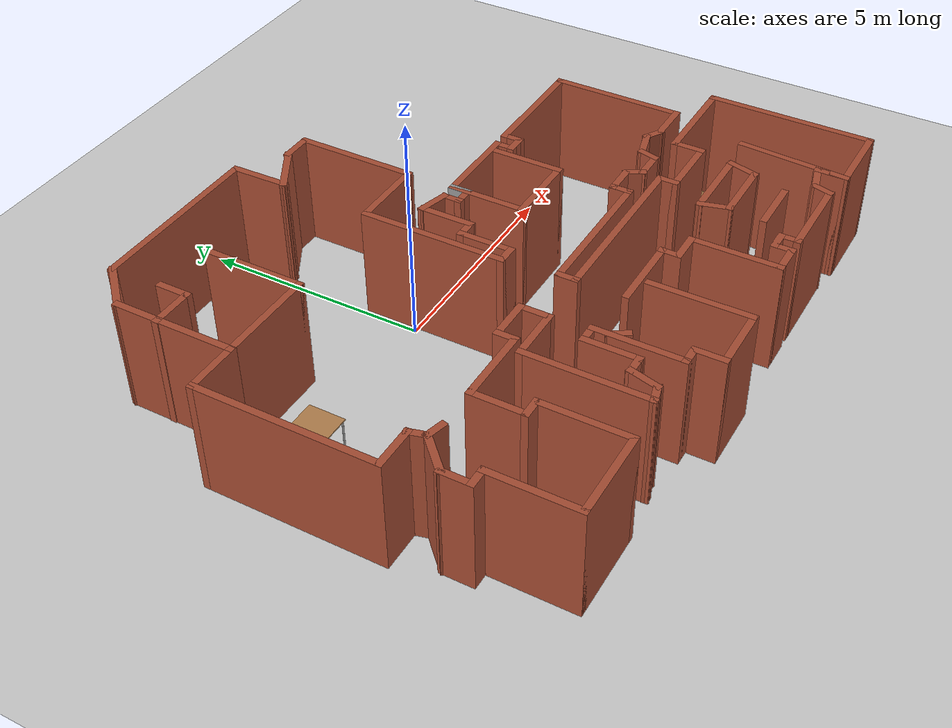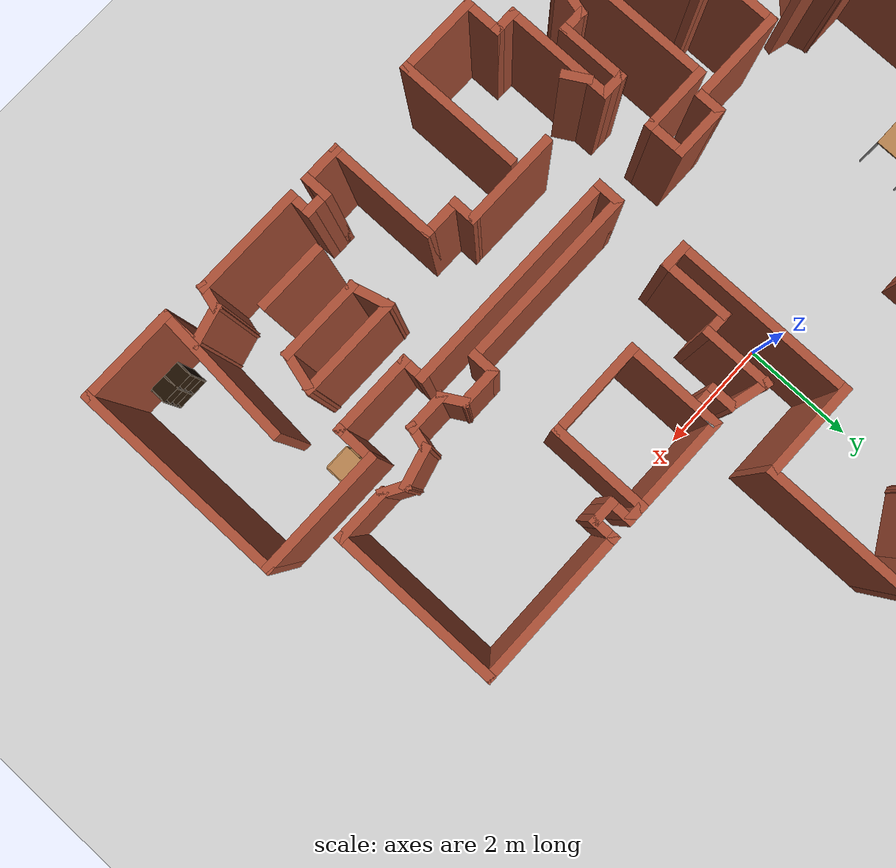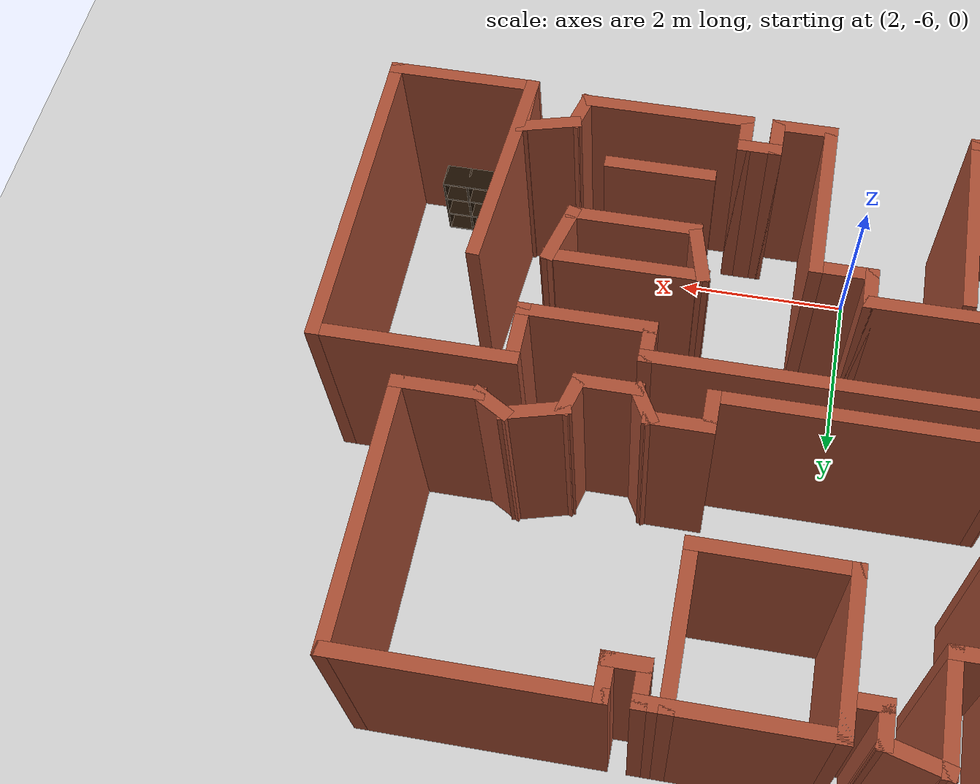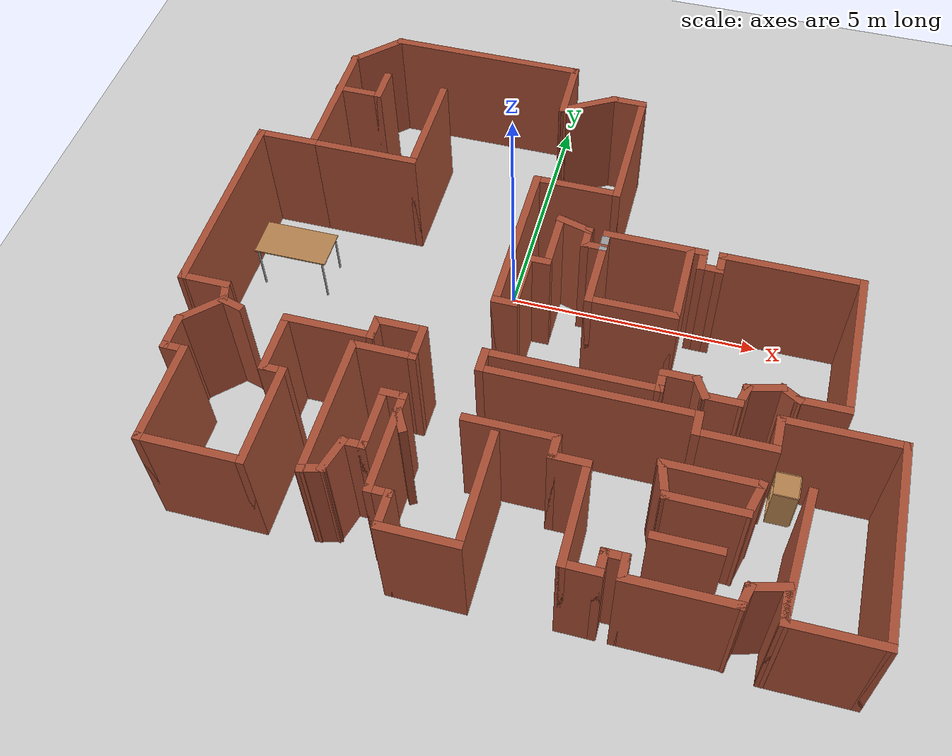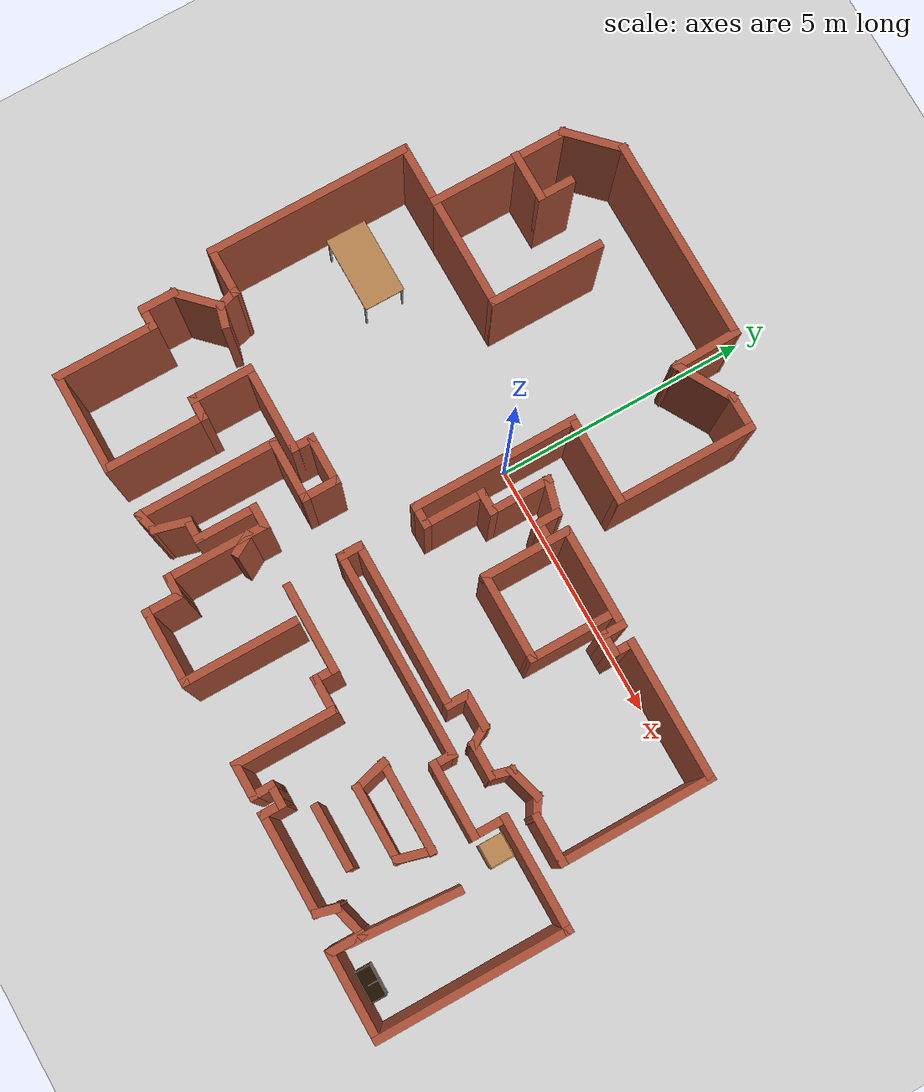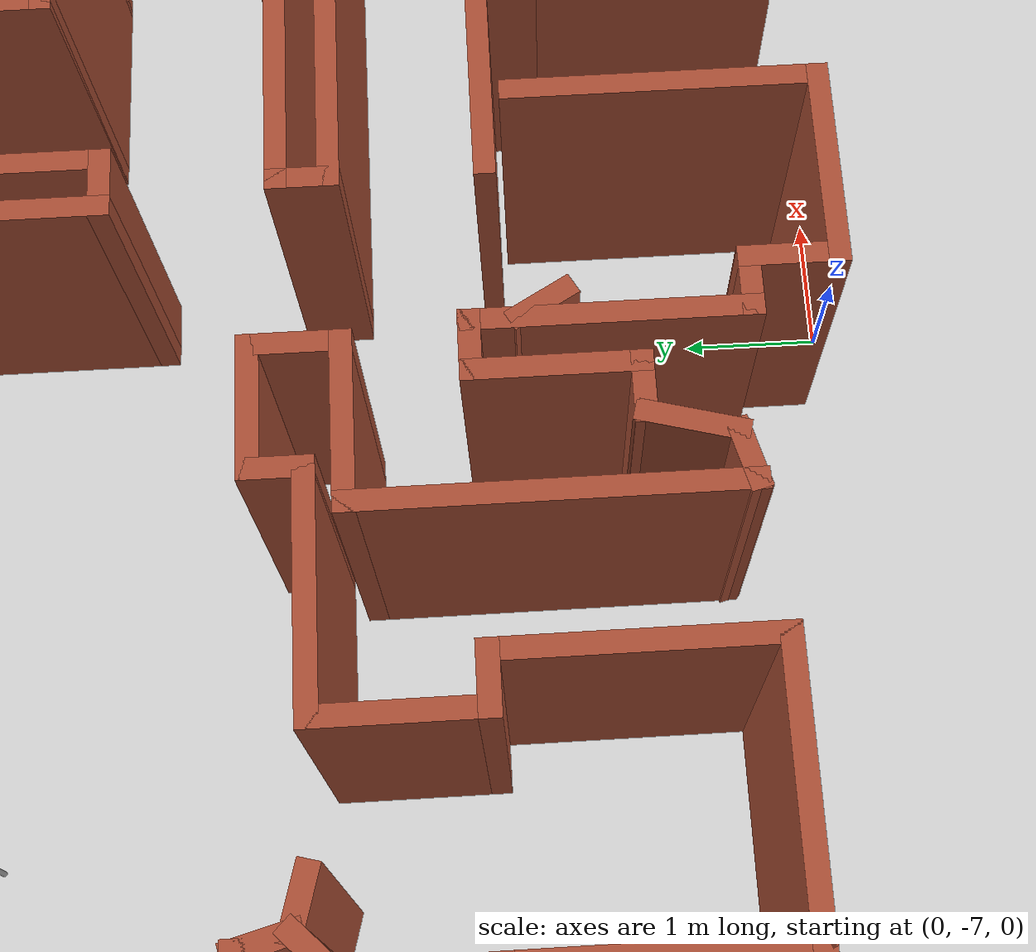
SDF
<sdf version="1.6">
 <world name="default">
  <light name="sun" type="directional">
   <pose>0 0 10 0 -0 0</pose>
   <diffuse>0.8 0.8 0.8 1</diffuse>
   <specular>0.2 0.2 0.2 1</specular>
   <attenuation>
    <range>1000</range>
    <constant>0.9</constant>
    <linear>0.01</linear>
    <quadratic>0.001</quadratic>
   </attenuation>
   <direction>-0.5 0.1 -0.9</direction>
  </light>
  <model name="ground_plane">
   <static>1</static>
   <link name="link">
    <collision name="collision">
     <geometry><plane><normal>0 0 1</normal><size>100 100</size></plane></geometry>
     <surface>
      <contact><collide_bitmask>65535</collide_bitmask></contact>
      <friction><ode><mu>100</mu><mu2>50</mu2></ode></friction>
     </surface>
    </collision>
    <visual name="visual">
     <cast_shadows>0</cast_shadows>
     <geometry><plane><normal>0 0 1</normal><size>100 100</size></plane></geometry>
     <material>
      <script><uri>file://media/materials/scripts/gazebo.material</uri><name>Gazebo/Grey</name></script>
     </material>
    </visual>
   </link>
  </model>
  <gravity>0 0 -9.8</gravity>
  <magnetic_field>6e-06 2.3e-05 -4.2e-05</magnetic_field>
  <atmosphere type="adiabatic"/>
  <physics name="default_physics" default="0" type="ode">
   <max_step_size>0.001</max_step_size>
   <real_time_factor>1</real_time_factor>
   <real_time_update_rate>1000</real_time_update_rate>
  </physics>
  <scene><ambient>0.4 0.4 0.4 1</ambient><background>0.7 0.7 0.7 1</background><shadows>1</shadows></scene>
  <audio><device>default</device></audio>
  <spherical_coordinates>
   <surface_model>EARTH_WGS84</surface_model>
   <latitude_deg>0</latitude_deg>
   <longitude_deg>0</longitude_deg>
   <elevation>0</elevation>
   <heading_deg>0</heading_deg>
  </spherical_coordinates>
  <model name="map_50">
   <pose>1.03793 -1.19697 0 0 -0 0</pose>
   <link name="Wall_0">
    <collision name="Wall_0_Collision">
     <geometry><box><size>4 0.15 2.5</size></box></geometry>
     <pose>0 0 1.25 0 -0 0</pose>
    </collision>
    <visual name="Wall_0_Visual">
     <pose>0 0 1.25 0 -0 0</pose>
     <geometry><box><size>4 0.15 2.5</size></box></geometry>
     <material>
      <script><uri>file://media/materials/scripts/gazebo.material</uri><name>Gazebo/Bricks</name></script>
      <ambient>1 1 1 1</ambient>
     </material>
     <meta><layer>0</layer></meta>
    </visual>
    <pose>-2.76652 5.59051 0 0 -0 3.14159</pose>
   </link>
   <link name="Wall_1">
    <collision name="Wall_1_Collision">
     <geometry><box><size>1.25 0.15 2.5</size></box></geometry>
     <pose>0 0 1.25 0 -0 0</pose>
    </collision>
    <visual name="Wall_1_Visual">
     <pose>0 0 1.25 0 -0 0</pose>
     <geometry><box><size>1.25 0.15 2.5</size></box></geometry>
     <material>
      <script><uri>file://media/materials/scripts/gazebo.material</uri><name>Gazebo/Bricks</name></script>
      <ambient>1 1 1 1</ambient>
     </material>
     <meta><layer>0</layer></meta>
    </visual>
    <pose>-5.08043 5.2016 0 0 -0 -2.35619</pose>
   </link>
   <link name="Wall_10">
    <collision name="Wall_10_Collision">
     <geometry><box><size>4 0.15 2.5</size></box></geometry>
     <pose>0 0 1.25 0 -0 0</pose>
    </collision>
    <visual name="Wall_10_Visual">
     <pose>0 0 1.25 0 -0 0</pose>
     <geometry><box><size>4 0.15 2.5</size></box></geometry>
     <material>
      <script><uri>file://media/materials/scripts/gazebo.material</uri><name>Gazebo/Bricks</name></script>
      <ambient>1 1 1 1</ambient>
     </material>
     <meta><layer>0</layer></meta>
    </visual>
    <pose>-6.56934 0.28769 0 0 -0 -1.5708</pose>
   </link>
   <link name="Wall_100">
    <collision name="Wall_100_Collision">
     <geometry><box><size>1.33662 0.15 2.5</size></box></geometry>
     <pose>0 0 1.25 0 -0 0</pose>
    </collision>
    <visual name="Wall_100_Visual">
     <pose>0 0 1.25 0 -0 0</pose>
     <geometry><box><size>1.33662 0.15 2.5</size></box></geometry>
     <material>
      <script><uri>file://media/materials/scripts/gazebo.material</uri><name>Gazebo/Bricks</name></script>
      <ambient>1 1 1 1</ambient>
     </material>
     <meta><layer>0</layer></meta>
    </visual>
    <pose>-0.828058 4.99735 0 0 -0 1.59349</pose>
   </link>
   <link name="Wall_102">
    <collision name="Wall_102_Collision">
     <geometry><box><size>1.75 0.15 2.5</size></box></geometry>
     <pose>0 0 1.25 0 -0 0</pose>
    </collision>
    <visual name="Wall_102_Visual">
     <pose>0 0 1.25 0 -0 0</pose>
     <geometry><box><size>1.75 0.15 2.5</size></box></geometry>
     <material>
      <script><uri>file://media/materials/scripts/gazebo.material</uri><name>Gazebo/Bricks</name></script>
      <ambient>1 1 1 1</ambient>
     </material>
     <meta><layer>0</layer></meta>
    </visual>
    <pose>0.767588 0.498903 0 0 -0 -1.5708</pose>
   </link>
   <link name="Wall_103">
    <collision name="Wall_103_Collision">
     <geometry><box><size>1.75 0.15 2.5</size></box></geometry>
     <pose>0 0 1.25 0 -0 0</pose>
    </collision>
    <visual name="Wall_103_Visual">
     <pose>0 0 1.25 0 -0 0</pose>
     <geometry><box><size>1.75 0.15 2.5</size></box></geometry>
     <material>
      <script><uri>file://media/materials/scripts/gazebo.material</uri><name>Gazebo/Bricks</name></script>
      <ambient>1 1 1 1</ambient>
     </material>
     <meta><layer>0</layer></meta>
    </visual>
    <pose>1.56759 -0.301097 0 0 -0 0</pose>
   </link>
   <link name="Wall_105">
    <collision name="Wall_105_Collision">
     <geometry><box><size>1.75 0.15 2.5</size></box></geometry>
     <pose>0 0 1.25 0 -0 0</pose>
    </collision>
    <visual name="Wall_105_Visual">
     <pose>0 0 1.25 0 -0 0</pose>
     <geometry><box><size>1.75 0.15 2.5</size></box></geometry>
     <material>
      <script><uri>file://media/materials/scripts/gazebo.material</uri><name>Gazebo/Bricks</name></script>
      <ambient>1 1 1 1</ambient>
     </material>
     <meta><layer>0</layer></meta>
    </visual>
    <pose>2.36759 0.498903 0 0 -0 1.5708</pose>
   </link>
   <link name="Wall_107">
    <collision name="Wall_107_Collision">
     <geometry><box><size>2.49794 0.15 2.5</size></box></geometry>
     <pose>0 0 1.25 0 -0 0</pose>
    </collision>
    <visual name="Wall_107_Visual">
     <pose>0 0 1.25 0 -0 0</pose>
     <geometry><box><size>2.49794 0.15 2.5</size></box></geometry>
     <material>
      <script><uri>file://media/materials/scripts/gazebo.material</uri><name>Gazebo/Bricks</name></script>
      <ambient>1 1 1 1</ambient>
     </material>
     <meta><layer>0</layer></meta>
    </visual>
    <pose>5.0541 -4.44545 0 0 -0 -1.64306</pose>
   </link>
   <link name="Wall_109">
    <collision name="Wall_109_Collision">
     <geometry><box><size>0.5 0.15 2.5</size></box></geometry>
     <pose>0 0 1.25 0 -0 0</pose>
    </collision>
    <visual name="Wall_109_Visual">
     <pose>0 0 1.25 0 -0 0</pose>
     <geometry><box><size>0.5 0.15 2.5</size></box></geometry>
     <material>
      <script><uri>file://media/materials/scripts/gazebo.material</uri><name>Gazebo/Bricks</name></script>
      <ambient>1 1 1 1</ambient>
     </material>
     <meta><layer>0</layer></meta>
    </visual>
    <pose>-1.73903 -3.63717 0 0 -0 -1.0472</pose>
   </link>
   <link name="Wall_11">
    <collision name="Wall_11_Collision">
     <geometry><box><size>1 0.15 2.5</size></box></geometry>
     <pose>0 0 1.25 0 -0 0</pose>
    </collision>
    <visual name="Wall_11_Visual">
     <pose>0 0 1.25 0 -0 0</pose>
     <geometry><box><size>1 0.15 2.5</size></box></geometry>
     <material>
      <script><uri>file://media/materials/scripts/gazebo.material</uri><name>Gazebo/Bricks</name></script>
      <ambient>1 1 1 1</ambient>
     </material>
     <meta><layer>0</layer></meta>
    </visual>
    <pose>-6.14434 -1.63731 0 0 -0 0</pose>
   </link>
   <link name="Wall_111">
    <collision name="Wall_111_Collision">
     <geometry><box><size>0.5 0.15 2.5</size></box></geometry>
     <pose>0 0 1.25 0 -0 0</pose>
    </collision>
    <visual name="Wall_111_Visual">
     <pose>0 0 1.25 0 -0 0</pose>
     <geometry><box><size>0.5 0.15 2.5</size></box></geometry>
     <material>
      <script><uri>file://media/materials/scripts/gazebo.material</uri><name>Gazebo/Bricks</name></script>
      <ambient>1 1 1 1</ambient>
     </material>
     <meta><layer>0</layer></meta>
    </visual>
    <pose>-5.45971 -2.02068 0 0 -0 -0.261799</pose>
   </link>
   <link name="Wall_113">
    <collision name="Wall_113_Collision">
     <geometry><box><size>1.25 0.15 2.5</size></box></geometry>
     <pose>0 0 1.25 0 -0 0</pose>
    </collision>
    <visual name="Wall_113_Visual">
     <pose>0 0 1.25 0 -0 0</pose>
     <geometry><box><size>1.25 0.15 2.5</size></box></geometry>
     <material>
      <script><uri>file://media/materials/scripts/gazebo.material</uri><name>Gazebo/Bricks</name></script>
      <ambient>1 1 1 1</ambient>
     </material>
     <meta><layer>0</layer></meta>
    </visual>
    <pose>3.33189 -4.68169 0 0 -0 0</pose>
   </link>
   <link name="Wall_115">
    <collision name="Wall_115_Collision">
     <geometry><box><size>0.75 0.15 2.5</size></box></geometry>
     <pose>0 0 1.25 0 -0 0</pose>
    </collision>
    <visual name="Wall_115_Visual">
     <pose>0 0 1.25 0 -0 0</pose>
     <geometry><box><size>0.75 0.15 2.5</size></box></geometry>
     <material>
      <script><uri>file://media/materials/scripts/gazebo.material</uri><name>Gazebo/Bricks</name></script>
      <ambient>1 1 1 1</ambient>
     </material>
     <meta><layer>0</layer></meta>
    </visual>
    <pose>2.754 -3.63468 0 0 -0 -1.309</pose>
   </link>
   <link name="Wall_116">
    <collision name="Wall_116_Collision">
     <geometry><box><size>1.5 0.15 2.5</size></box></geometry>
     <pose>0 0 1.25 0 -0 0</pose>
    </collision>
    <visual name="Wall_116_Visual">
     <pose>0 0 1.25 0 -0 0</pose>
     <geometry><box><size>1.5 0.15 2.5</size></box></geometry>
     <material>
      <script><uri>file://media/materials/scripts/gazebo.material</uri><name>Gazebo/Bricks</name></script>
      <ambient>1 1 1 1</ambient>
     </material>
     <meta><layer>0</layer></meta>
    </visual>
    <pose>3.50665 -3.92445 0 0 -0 0</pose>
   </link>
   <link name="Wall_117">
    <collision name="Wall_117_Collision">
     <geometry><box><size>0.75 0.15 2.5</size></box></geometry>
     <pose>0 0 1.25 0 -0 0</pose>
    </collision>
    <visual name="Wall_117_Visual">
     <pose>0 0 1.25 0 -0 0</pose>
     <geometry><box><size>0.75 0.15 2.5</size></box></geometry>
     <material>
      <script><uri>file://media/materials/scripts/gazebo.material</uri><name>Gazebo/Bricks</name></script>
      <ambient>1 1 1 1</ambient>
     </material>
     <meta><layer>0</layer></meta>
    </visual>
    <pose>4.25929 -3.63468 0 0 -0 1.309</pose>
   </link>
   <link name="Wall_118">
    <collision name="Wall_118_Collision">
     <geometry><box><size>1.81058 0.15 2.5</size></box></geometry>
     <pose>0 0 1.25 0 -0 0</pose>
    </collision>
    <visual name="Wall_118_Visual">
     <pose>0 0 1.25 0 -0 0</pose>
     <geometry><box><size>1.81058 0.15 2.5</size></box></geometry>
     <material>
      <script><uri>file://media/materials/scripts/gazebo.material</uri><name>Gazebo/Bricks</name></script>
      <ambient>1 1 1 1</ambient>
     </material>
     <meta><layer>0</layer></meta>
    </visual>
    <pose>3.50665 -3.3449 0 0 -0 3.14159</pose>
   </link>
   <link name="Wall_12">
    <collision name="Wall_12_Collision">
     <geometry><box><size>0.5 0.15 2.5</size></box></geometry>
     <pose>0 0 1.25 0 -0 0</pose>
    </collision>
    <visual name="Wall_12_Visual">
     <pose>0 0 1.25 0 -0 0</pose>
     <geometry><box><size>0.5 0.15 2.5</size></box></geometry>
     <material>
      <script><uri>file://media/materials/scripts/gazebo.material</uri><name>Gazebo/Bricks</name></script>
      <ambient>1 1 1 1</ambient>
     </material>
     <meta><layer>0</layer></meta>
    </visual>
    <pose>-5.67404 -1.80635 0 0 -0 -1.309</pose>
   </link>
   <link name="Wall_13">
    <collision name="Wall_13_Collision">
     <geometry><box><size>1 0.15 2.5</size></box></geometry>
     <pose>0 0 1.25 0 -0 0</pose>
    </collision>
    <visual name="Wall_13_Visual">
     <pose>0 0 1.25 0 -0 0</pose>
     <geometry><box><size>1 0.15 2.5</size></box></geometry>
     <material>
      <script><uri>file://media/materials/scripts/gazebo.material</uri><name>Gazebo/Bricks</name></script>
      <ambient>1 1 1 1</ambient>
     </material>
     <meta><layer>0</layer></meta>
    </visual>
    <pose>-5.92927 -2.2759 0 0 -0 -2.35619</pose>
   </link>
   <link name="Wall_14">
    <collision name="Wall_14_Collision">
     <geometry><box><size>0.75 0.15 2.5</size></box></geometry>
     <pose>0 0 1.25 0 -0 0</pose>
    </collision>
    <visual name="Wall_14_Visual">
     <pose>0 0 1.25 0 -0 0</pose>
     <geometry><box><size>0.75 0.15 2.5</size></box></geometry>
     <material>
      <script><uri>file://media/materials/scripts/gazebo.material</uri><name>Gazebo/Bricks</name></script>
      <ambient>1 1 1 1</ambient>
     </material>
     <meta><layer>0</layer></meta>
    </visual>
    <pose>-6.22979 -2.87642 0 0 -0 -1.5708</pose>
   </link>
   <link name="Wall_15">
    <collision name="Wall_15_Collision">
     <geometry><box><size>0.5 0.15 2.5</size></box></geometry>
     <pose>0 0 1.25 0 -0 0</pose>
    </collision>
    <visual name="Wall_15_Visual">
     <pose>0 0 1.25 0 -0 0</pose>
     <geometry><box><size>0.5 0.15 2.5</size></box></geometry>
     <material>
      <script><uri>file://media/materials/scripts/gazebo.material</uri><name>Gazebo/Bricks</name></script>
      <ambient>1 1 1 1</ambient>
     </material>
     <meta><layer>0</layer></meta>
    </visual>
    <pose>-6.05479 -3.17643 0 0 -0 0</pose>
   </link>
   <link name="Wall_16">
    <collision name="Wall_16_Collision">
     <geometry><box><size>2 0.15 2.5</size></box></geometry>
     <pose>0 0 1.25 0 -0 0</pose>
    </collision>
    <visual name="Wall_16_Visual">
     <pose>0 0 1.25 0 -0 0</pose>
     <geometry><box><size>2 0.15 2.5</size></box></geometry>
     <material>
      <script><uri>file://media/materials/scripts/gazebo.material</uri><name>Gazebo/Bricks</name></script>
      <ambient>1 1 1 1</ambient>
     </material>
     <meta><layer>0</layer></meta>
    </visual>
    <pose>-5.87979 -4.10142 0 0 -0 -1.5708</pose>
   </link>
   <link name="Wall_17">
    <collision name="Wall_17_Collision">
     <geometry><box><size>2 0.15 2.5</size></box></geometry>
     <pose>0 0 1.25 0 -0 0</pose>
    </collision>
    <visual name="Wall_17_Visual">
     <pose>0 0 1.25 0 -0 0</pose>
     <geometry><box><size>2 0.15 2.5</size></box></geometry>
     <material>
      <script><uri>file://media/materials/scripts/gazebo.material</uri><name>Gazebo/Bricks</name></script>
      <ambient>1 1 1 1</ambient>
     </material>
     <meta><layer>0</layer></meta>
    </visual>
    <pose>-4.95479 -5.02642 0 0 -0 0</pose>
   </link>
   <link name="Wall_18">
    <collision name="Wall_18_Collision">
     <geometry><box><size>2 0.15 2.5</size></box></geometry>
     <pose>0 0 1.25 0 -0 0</pose>
    </collision>
    <visual name="Wall_18_Visual">
     <pose>0 0 1.25 0 -0 0</pose>
     <geometry><box><size>2 0.15 2.5</size></box></geometry>
     <material>
      <script><uri>file://media/materials/scripts/gazebo.material</uri><name>Gazebo/Bricks</name></script>
      <ambient>1 1 1 1</ambient>
     </material>
     <meta><layer>0</layer></meta>
    </visual>
    <pose>-4.02979 -4.10142 0 0 -0 1.5708</pose>
   </link>
   <link name="Wall_19">
    <collision name="Wall_19_Collision">
     <geometry><box><size>0.5 0.15 2.5</size></box></geometry>
     <pose>0 0 1.25 0 -0 0</pose>
    </collision>
    <visual name="Wall_19_Visual">
     <pose>0 0 1.25 0 -0 0</pose>
     <geometry><box><size>0.5 0.15 2.5</size></box></geometry>
     <material>
      <script><uri>file://media/materials/scripts/gazebo.material</uri><name>Gazebo/Bricks</name></script>
      <ambient>1 1 1 1</ambient>
     </material>
     <meta><layer>0</layer></meta>
    </visual>
    <pose>-4.20479 -3.17643 0 0 -0 3.14159</pose>
   </link>
   <link name="Wall_2">
    <collision name="Wall_2_Collision">
     <geometry><box><size>2.75 0.15 2.5</size></box></geometry>
     <pose>0 0 1.25 0 -0 0</pose>
    </collision>
    <visual name="Wall_2_Visual">
     <pose>0 0 1.25 0 -0 0</pose>
     <geometry><box><size>2.75 0.15 2.5</size></box></geometry>
     <material>
      <script><uri>file://media/materials/scripts/gazebo.material</uri><name>Gazebo/Bricks</name></script>
      <ambient>1 1 1 1</ambient>
     </material>
     <meta><layer>0</layer></meta>
    </visual>
    <pose>-5.46934 3.51269 0 0 -0 -1.5708</pose>
   </link>
   <link name="Wall_20">
    <collision name="Wall_20_Collision">
     <geometry><box><size>1.25 0.15 2.5</size></box></geometry>
     <pose>0 0 1.25 0 -0 0</pose>
    </collision>
    <visual name="Wall_20_Visual">
     <pose>0 0 1.25 0 -0 0</pose>
     <geometry><box><size>1.25 0.15 2.5</size></box></geometry>
     <material>
      <script><uri>file://media/materials/scripts/gazebo.material</uri><name>Gazebo/Bricks</name></script>
      <ambient>1 1 1 1</ambient>
     </material>
     <meta><layer>0</layer></meta>
    </visual>
    <pose>-4.37979 -2.62642 0 0 -0 1.5708</pose>
   </link>
   <link name="Wall_21">
    <collision name="Wall_21_Collision">
     <geometry><box><size>1.75 0.15 2.5</size></box></geometry>
     <pose>0 0 1.25 0 -0 0</pose>
    </collision>
    <visual name="Wall_21_Visual">
     <pose>0 0 1.25 0 -0 0</pose>
     <geometry><box><size>1.75 0.15 2.5</size></box></geometry>
     <material>
      <script><uri>file://media/materials/scripts/gazebo.material</uri><name>Gazebo/Bricks</name></script>
      <ambient>1 1 1 1</ambient>
     </material>
     <meta><layer>0</layer></meta>
    </visual>
    <pose>-3.57979 -2.07642 0 0 -0 0</pose>
   </link>
   <link name="Wall_22">
    <collision name="Wall_22_Collision">
     <geometry><box><size>0.5 0.15 2.5</size></box></geometry>
     <pose>0 0 1.25 0 -0 0</pose>
    </collision>
    <visual name="Wall_22_Visual">
     <pose>0 0 1.25 0 -0 0</pose>
     <geometry><box><size>0.5 0.15 2.5</size></box></geometry>
     <material>
      <script><uri>file://media/materials/scripts/gazebo.material</uri><name>Gazebo/Bricks</name></script>
      <ambient>1 1 1 1</ambient>
     </material>
     <meta><layer>0</layer></meta>
    </visual>
    <pose>-2.77979 -1.90142 0 0 -0 1.5708</pose>
   </link>
   <link name="Wall_23">
    <collision name="Wall_23_Collision">
     <geometry><box><size>1 0.15 2.5</size></box></geometry>
     <pose>0 0 1.25 0 -0 0</pose>
    </collision>
    <visual name="Wall_23_Visual">
     <pose>0 0 1.25 0 -0 0</pose>
     <geometry><box><size>1 0.15 2.5</size></box></geometry>
     <material>
      <script><uri>file://media/materials/scripts/gazebo.material</uri><name>Gazebo/Bricks</name></script>
      <ambient>1 1 1 1</ambient>
     </material>
     <meta><layer>0</layer></meta>
    </visual>
    <pose>-2.35479 -1.72642 0 0 -0 0</pose>
   </link>
   <link name="Wall_24">
    <collision name="Wall_24_Collision">
     <geometry><box><size>0.75 0.15 2.5</size></box></geometry>
     <pose>0 0 1.25 0 -0 0</pose>
    </collision>
    <visual name="Wall_24_Visual">
     <pose>0 0 1.25 0 -0 0</pose>
     <geometry><box><size>0.75 0.15 2.5</size></box></geometry>
     <material>
      <script><uri>file://media/materials/scripts/gazebo.material</uri><name>Gazebo/Bricks</name></script>
      <ambient>1 1 1 1</ambient>
     </material>
     <meta><layer>0</layer></meta>
    </visual>
    <pose>-1.92979 -2.02643 0 0 -0 -1.5708</pose>
   </link>
   <link name="Wall_25">
    <collision name="Wall_25_Collision">
     <geometry><box><size>1.25 0.15 2.5</size></box></geometry>
     <pose>0 0 1.25 0 -0 0</pose>
    </collision>
    <visual name="Wall_25_Visual">
     <pose>0 0 1.25 0 -0 0</pose>
     <geometry><box><size>1.25 0.15 2.5</size></box></geometry>
     <material>
      <script><uri>file://media/materials/scripts/gazebo.material</uri><name>Gazebo/Bricks</name></script>
      <ambient>1 1 1 1</ambient>
     </material>
     <meta><layer>0</layer></meta>
    </visual>
    <pose>-2.47979 -2.32642 0 0 -0 3.14159</pose>
   </link>
   <link name="Wall_26">
    <collision name="Wall_26_Collision">
     <geometry><box><size>2.75 0.15 2.5</size></box></geometry>
     <pose>0 0 1.25 0 -0 0</pose>
    </collision>
    <visual name="Wall_26_Visual">
     <pose>0 0 1.25 0 -0 0</pose>
     <geometry><box><size>2.75 0.15 2.5</size></box></geometry>
     <material>
      <script><uri>file://media/materials/scripts/gazebo.material</uri><name>Gazebo/Bricks</name></script>
      <ambient>1 1 1 1</ambient>
     </material>
     <meta><layer>0</layer></meta>
    </visual>
    <pose>-3.02979 -3.62642 0 0 -0 -1.5708</pose>
   </link>
   <link name="Wall_27">
    <collision name="Wall_27_Collision">
     <geometry><box><size>0.5 0.15 2.5</size></box></geometry>
     <pose>0 0 1.25 0 -0 0</pose>
    </collision>
    <visual name="Wall_27_Visual">
     <pose>0 0 1.25 0 -0 0</pose>
     <geometry><box><size>0.5 0.15 2.5</size></box></geometry>
     <material>
      <script><uri>file://media/materials/scripts/gazebo.material</uri><name>Gazebo/Bricks</name></script>
      <ambient>1 1 1 1</ambient>
     </material>
     <meta><layer>0</layer></meta>
    </visual>
    <pose>-2.86076 -4.88113 0 0 -0 0.261799</pose>
   </link>
   <link name="Wall_28">
    <collision name="Wall_28_Collision">
     <geometry><box><size>0.75 0.15 2.5</size></box></geometry>
     <pose>0 0 1.25 0 -0 0</pose>
    </collision>
    <visual name="Wall_28_Visual">
     <pose>0 0 1.25 0 -0 0</pose>
     <geometry><box><size>0.75 0.15 2.5</size></box></geometry>
     <material>
      <script><uri>file://media/materials/scripts/gazebo.material</uri><name>Gazebo/Bricks</name></script>
      <ambient>1 1 1 1</ambient>
     </material>
     <meta><layer>0</layer></meta>
    </visual>
    <pose>-2.61407 -4.54606 0 0 -0 1.309</pose>
   </link>
   <link name="Wall_3">
    <collision name="Wall_3_Collision">
     <geometry><box><size>2.25 0.15 2.5</size></box></geometry>
     <pose>0 0 1.25 0 -0 0</pose>
    </collision>
    <visual name="Wall_3_Visual">
     <pose>0 0 1.25 0 -0 0</pose>
     <geometry><box><size>2.25 0.15 2.5</size></box></geometry>
     <material>
      <script><uri>file://media/materials/scripts/gazebo.material</uri><name>Gazebo/Bricks</name></script>
      <ambient>1 1 1 1</ambient>
     </material>
     <meta><layer>0</layer></meta>
    </visual>
    <pose>-4.41934 2.21269 0 0 -0 0</pose>
   </link>
   <link name="Wall_33">
    <collision name="Wall_33_Collision">
     <geometry><box><size>0.5 0.15 2.5</size></box></geometry>
     <pose>0 0 1.25 0 -0 0</pose>
    </collision>
    <visual name="Wall_33_Visual">
     <pose>0 0 1.25 0 -0 0</pose>
     <geometry><box><size>0.5 0.15 2.5</size></box></geometry>
     <material>
      <script><uri>file://media/materials/scripts/gazebo.material</uri><name>Gazebo/Bricks</name></script>
      <ambient>1 1 1 1</ambient>
     </material>
     <meta><layer>0</layer></meta>
    </visual>
    <pose>-2.36143 -4.25628 0 0 -0 0</pose>
   </link>
   <link name="Wall_34">
    <collision name="Wall_34_Collision">
     <geometry><box><size>1.25 0.15 2.5</size></box></geometry>
     <pose>0 0 1.25 0 -0 0</pose>
    </collision>
    <visual name="Wall_34_Visual">
     <pose>0 0 1.25 0 -0 0</pose>
     <geometry><box><size>1.25 0.15 2.5</size></box></geometry>
     <material>
      <script><uri>file://media/materials/scripts/gazebo.material</uri><name>Gazebo/Bricks</name></script>
      <ambient>1 1 1 1</ambient>
     </material>
     <meta><layer>0</layer></meta>
    </visual>
    <pose>-2.18643 -3.70628 0 0 -0 1.5708</pose>
   </link>
   <link name="Wall_35">
    <collision name="Wall_35_Collision">
     <geometry><box><size>0.5 0.15 2.5</size></box></geometry>
     <pose>0 0 1.25 0 -0 0</pose>
    </collision>
    <visual name="Wall_35_Visual">
     <pose>0 0 1.25 0 -0 0</pose>
     <geometry><box><size>0.5 0.15 2.5</size></box></geometry>
     <material>
      <script><uri>file://media/materials/scripts/gazebo.material</uri><name>Gazebo/Bricks</name></script>
      <ambient>1 1 1 1</ambient>
     </material>
     <meta><layer>0</layer></meta>
    </visual>
    <pose>-2.01143 -3.15628 0 0 -0 0</pose>
   </link>
   <link name="Wall_36">
    <collision name="Wall_36_Collision">
     <geometry><box><size>2 0.15 2.5</size></box></geometry>
     <pose>0 0 1.25 0 -0 0</pose>
    </collision>
    <visual name="Wall_36_Visual">
     <pose>0 0 1.25 0 -0 0</pose>
     <geometry><box><size>2 0.15 2.5</size></box></geometry>
     <material>
      <script><uri>file://media/materials/scripts/gazebo.material</uri><name>Gazebo/Bricks</name></script>
      <ambient>1 1 1 1</ambient>
     </material>
     <meta><layer>0</layer></meta>
    </visual>
    <pose>-1.83643 -4.08128 0 0 -0 -1.5708</pose>
   </link>
   <link name="Wall_37">
    <collision name="Wall_37_Collision">
     <geometry><box><size>0.5 0.15 2.5</size></box></geometry>
     <pose>0 0 1.25 0 -0 0</pose>
    </collision>
    <visual name="Wall_37_Visual">
     <pose>0 0 1.25 0 -0 0</pose>
     <geometry><box><size>0.5 0.15 2.5</size></box></geometry>
     <material>
      <script><uri>file://media/materials/scripts/gazebo.material</uri><name>Gazebo/Bricks</name></script>
      <ambient>1 1 1 1</ambient>
     </material>
     <meta><layer>0</layer></meta>
    </visual>
    <pose>-1.66143 -5.00628 0 0 -0 0</pose>
   </link>
   <link name="Wall_38">
    <collision name="Wall_38_Collision">
     <geometry><box><size>0.75 0.15 2.5</size></box></geometry>
     <pose>0 0 1.25 0 -0 0</pose>
    </collision>
    <visual name="Wall_38_Visual">
     <pose>0 0 1.25 0 -0 0</pose>
     <geometry><box><size>0.75 0.15 2.5</size></box></geometry>
     <material>
      <script><uri>file://media/materials/scripts/gazebo.material</uri><name>Gazebo/Bricks</name></script>
      <ambient>1 1 1 1</ambient>
     </material>
     <meta><layer>0</layer></meta>
    </visual>
    <pose>-1.48643 -5.30628 0 0 -0 -1.5708</pose>
   </link>
   <link name="Wall_4">
    <collision name="Wall_4_Collision">
     <geometry><box><size>2.25 0.15 2.5</size></box></geometry>
     <pose>0 0 1.25 0 -0 0</pose>
    </collision>
    <visual name="Wall_4_Visual">
     <pose>0 0 1.25 0 -0 0</pose>
     <geometry><box><size>2.25 0.15 2.5</size></box></geometry>
     <material>
      <script><uri>file://media/materials/scripts/gazebo.material</uri><name>Gazebo/Bricks</name></script>
      <ambient>1 1 1 1</ambient>
     </material>
     <meta><layer>0</layer></meta>
    </visual>
    <pose>-3.36934 3.26269 0 0 -0 1.5708</pose>
   </link>
   <link name="Wall_41">
    <collision name="Wall_41_Collision">
     <geometry><box><size>1.5 0.15 2.5</size></box></geometry>
     <pose>0 0 1.25 0 -0 0</pose>
    </collision>
    <visual name="Wall_41_Visual">
     <pose>0 0 1.25 0 -0 0</pose>
     <geometry><box><size>1.5 0.15 2.5</size></box></geometry>
     <material>
      <script><uri>file://media/materials/scripts/gazebo.material</uri><name>Gazebo/Bricks</name></script>
      <ambient>1 1 1 1</ambient>
     </material>
     <meta><layer>0</layer></meta>
    </visual>
    <pose>-0.811426 -5.60628 0 0 -0 0</pose>
   </link>
   <link name="Wall_42">
    <collision name="Wall_42_Collision">
     <geometry><box><size>2.25 0.15 2.5</size></box></geometry>
     <pose>0 0 1.25 0 -0 0</pose>
    </collision>
    <visual name="Wall_42_Visual">
     <pose>0 0 1.25 0 -0 0</pose>
     <geometry><box><size>2.25 0.15 2.5</size></box></geometry>
     <material>
      <script><uri>file://media/materials/scripts/gazebo.material</uri><name>Gazebo/Bricks</name></script>
      <ambient>1 1 1 1</ambient>
     </material>
     <meta><layer>0</layer></meta>
    </visual>
    <pose>-0.136426 -4.55628 0 0 -0 1.5708</pose>
   </link>
   <link name="Wall_44">
    <collision name="Wall_44_Collision">
     <geometry><box><size>1.75 0.15 2.5</size></box></geometry>
     <pose>0 0 1.25 0 -0 0</pose>
    </collision>
    <visual name="Wall_44_Visual">
     <pose>0 0 1.25 0 -0 0</pose>
     <geometry><box><size>1.75 0.15 2.5</size></box></geometry>
     <material>
      <script><uri>file://media/materials/scripts/gazebo.material</uri><name>Gazebo/Bricks</name></script>
      <ambient>1 1 1 1</ambient>
     </material>
     <meta><layer>0</layer></meta>
    </visual>
    <pose>0.099195 -3.30972 0 0 -0 0</pose>
   </link>
   <link name="Wall_45">
    <collision name="Wall_45_Collision">
     <geometry><box><size>0.5 0.15 2.5</size></box></geometry>
     <pose>0 0 1.25 0 -0 0</pose>
    </collision>
    <visual name="Wall_45_Visual">
     <pose>0 0 1.25 0 -0 0</pose>
     <geometry><box><size>0.5 0.15 2.5</size></box></geometry>
     <material>
      <script><uri>file://media/materials/scripts/gazebo.material</uri><name>Gazebo/Bricks</name></script>
      <ambient>1 1 1 1</ambient>
     </material>
     <meta><layer>0</layer></meta>
    </visual>
    <pose>0.899195 -3.48472 0 0 -0 -1.5708</pose>
   </link>
   <link name="Wall_46">
    <collision name="Wall_46_Collision">
     <geometry><box><size>0.75 0.15 2.5</size></box></geometry>
     <pose>0 0 1.25 0 -0 0</pose>
    </collision>
    <visual name="Wall_46_Visual">
     <pose>0 0 1.25 0 -0 0</pose>
     <geometry><box><size>0.75 0.15 2.5</size></box></geometry>
     <material>
      <script><uri>file://media/materials/scripts/gazebo.material</uri><name>Gazebo/Bricks</name></script>
      <ambient>1 1 1 1</ambient>
     </material>
     <meta><layer>0</layer></meta>
    </visual>
    <pose>1.1992 -3.65972 0 0 -0 0</pose>
   </link>
   <link name="Wall_47">
    <collision name="Wall_47_Collision">
     <geometry><box><size>2 0.15 2.5</size></box></geometry>
     <pose>0 0 1.25 0 -0 0</pose>
    </collision>
    <visual name="Wall_47_Visual">
     <pose>0 0 1.25 0 -0 0</pose>
     <geometry><box><size>2 0.15 2.5</size></box></geometry>
     <material>
      <script><uri>file://media/materials/scripts/gazebo.material</uri><name>Gazebo/Bricks</name></script>
      <ambient>1 1 1 1</ambient>
     </material>
     <meta><layer>0</layer></meta>
    </visual>
    <pose>1.4992 -4.58472 0 0 -0 -1.5708</pose>
   </link>
   <link name="Wall_48">
    <collision name="Wall_48_Collision">
     <geometry><box><size>0.75 0.15 2.5</size></box></geometry>
     <pose>0 0 1.25 0 -0 0</pose>
    </collision>
    <visual name="Wall_48_Visual">
     <pose>0 0 1.25 0 -0 0</pose>
     <geometry><box><size>0.75 0.15 2.5</size></box></geometry>
     <material>
      <script><uri>file://media/materials/scripts/gazebo.material</uri><name>Gazebo/Bricks</name></script>
      <ambient>1 1 1 1</ambient>
     </material>
     <meta><layer>0</layer></meta>
    </visual>
    <pose>1.7992 -5.50972 0 0 -0 0</pose>
   </link>
   <link name="Wall_49">
    <collision name="Wall_49_Collision">
     <geometry><box><size>0.5 0.15 2.5</size></box></geometry>
     <pose>0 0 1.25 0 -0 0</pose>
    </collision>
    <visual name="Wall_49_Visual">
     <pose>0 0 1.25 0 -0 0</pose>
     <geometry><box><size>0.5 0.15 2.5</size></box></geometry>
     <material>
      <script><uri>file://media/materials/scripts/gazebo.material</uri><name>Gazebo/Bricks</name></script>
      <ambient>1 1 1 1</ambient>
     </material>
     <meta><layer>0</layer></meta>
    </visual>
    <pose>2.09919 -5.33472 0 0 -0 1.5708</pose>
   </link>
   <link name="Wall_50">
    <collision name="Wall_50_Collision">
     <geometry><box><size>0.5 0.15 2.5</size></box></geometry>
     <pose>0 0 1.25 0 -0 0</pose>
    </collision>
    <visual name="Wall_50_Visual">
     <pose>0 0 1.25 0 -0 0</pose>
     <geometry><box><size>0.5 0.15 2.5</size></box></geometry>
     <material>
      <script><uri>file://media/materials/scripts/gazebo.material</uri><name>Gazebo/Bricks</name></script>
      <ambient>1 1 1 1</ambient>
     </material>
     <meta><layer>0</layer></meta>
    </visual>
    <pose>2.2742 -5.15972 0 0 -0 0</pose>
   </link>
   <link name="Wall_51">
    <collision name="Wall_51_Collision">
     <geometry><box><size>0.5 0.15 2.5</size></box></geometry>
     <pose>0 0 1.25 0 -0 0</pose>
    </collision>
    <visual name="Wall_51_Visual">
     <pose>0 0 1.25 0 -0 0</pose>
     <geometry><box><size>0.5 0.15 2.5</size></box></geometry>
     <material>
      <script><uri>file://media/materials/scripts/gazebo.material</uri><name>Gazebo/Bricks</name></script>
      <ambient>1 1 1 1</ambient>
     </material>
     <meta><layer>0</layer></meta>
    </visual>
    <pose>2.4492 -5.33472 0 0 -0 -1.5708</pose>
   </link>
   <link name="Wall_52">
    <collision name="Wall_52_Collision">
     <geometry><box><size>2 0.15 2.5</size></box></geometry>
     <pose>0 0 1.25 0 -0 0</pose>
    </collision>
    <visual name="Wall_52_Visual">
     <pose>0 0 1.25 0 -0 0</pose>
     <geometry><box><size>2 0.15 2.5</size></box></geometry>
     <material>
      <script><uri>file://media/materials/scripts/gazebo.material</uri><name>Gazebo/Bricks</name></script>
      <ambient>1 1 1 1</ambient>
     </material>
     <meta><layer>0</layer></meta>
    </visual>
    <pose>3.37419 -5.50972 0 0 -0 0</pose>
   </link>
   <link name="Wall_53">
    <collision name="Wall_53_Collision">
     <geometry><box><size>0.5 0.15 2.5</size></box></geometry>
     <pose>0 0 1.25 0 -0 0</pose>
    </collision>
    <visual name="Wall_53_Visual">
     <pose>0 0 1.25 0 -0 0</pose>
     <geometry><box><size>0.5 0.15 2.5</size></box></geometry>
     <material>
      <script><uri>file://media/materials/scripts/gazebo.material</uri><name>Gazebo/Bricks</name></script>
      <ambient>1 1 1 1</ambient>
     </material>
     <meta><layer>0</layer></meta>
    </visual>
    <pose>4.34449 -5.34068 0 0 -0 1.309</pose>
   </link>
   <link name="Wall_54">
    <collision name="Wall_54_Collision">
     <geometry><box><size>0.75 0.15 2.5</size></box></geometry>
     <pose>0 0 1.25 0 -0 0</pose>
    </collision>
    <visual name="Wall_54_Visual">
     <pose>0 0 1.25 0 -0 0</pose>
     <geometry><box><size>0.75 0.15 2.5</size></box></geometry>
     <material>
      <script><uri>file://media/materials/scripts/gazebo.material</uri><name>Gazebo/Bricks</name></script>
      <ambient>1 1 1 1</ambient>
     </material>
     <meta><layer>0</layer></meta>
    </visual>
    <pose>4.67956 -5.094 0 0 -0 0.261799</pose>
   </link>
   <link name="Wall_55">
    <collision name="Wall_55_Collision">
     <geometry><box><size>0.75 0.15 2.5</size></box></geometry>
     <pose>0 0 1.25 0 -0 0</pose>
    </collision>
    <visual name="Wall_55_Visual">
     <pose>0 0 1.25 0 -0 0</pose>
     <geometry><box><size>0.75 0.15 2.5</size></box></geometry>
     <material>
      <script><uri>file://media/materials/scripts/gazebo.material</uri><name>Gazebo/Bricks</name></script>
      <ambient>1 1 1 1</ambient>
     </material>
     <meta><layer>0</layer></meta>
    </visual>
    <pose>4.96934 -5.31635 0 0 -0 -1.5708</pose>
   </link>
   <link name="Wall_56">
    <collision name="Wall_56_Collision">
     <geometry><box><size>1.75 0.15 2.5</size></box></geometry>
     <pose>0 0 1.25 0 -0 0</pose>
    </collision>
    <visual name="Wall_56_Visual">
     <pose>0 0 1.25 0 -0 0</pose>
     <geometry><box><size>1.75 0.15 2.5</size></box></geometry>
     <material>
      <script><uri>file://media/materials/scripts/gazebo.material</uri><name>Gazebo/Bricks</name></script>
      <ambient>1 1 1 1</ambient>
     </material>
     <meta><layer>0</layer></meta>
    </visual>
    <pose>5.76934 -5.61635 0 0 -0 0</pose>
   </link>
   <link name="Wall_57">
    <collision name="Wall_57_Collision">
     <geometry><box><size>3.75 0.15 2.5</size></box></geometry>
     <pose>0 0 1.25 0 -0 0</pose>
    </collision>
    <visual name="Wall_57_Visual">
     <pose>0 0 1.25 0 -0 0</pose>
     <geometry><box><size>3.75 0.15 2.5</size></box></geometry>
     <material>
      <script><uri>file://media/materials/scripts/gazebo.material</uri><name>Gazebo/Bricks</name></script>
      <ambient>1 1 1 1</ambient>
     </material>
     <meta><layer>0</layer></meta>
    </visual>
    <pose>6.56934 -3.81635 0 0 -0 1.5708</pose>
   </link>
   <link name="Wall_58">
    <collision name="Wall_58_Collision">
     <geometry><box><size>2.25 0.15 2.5</size></box></geometry>
     <pose>0 0 1.25 0 -0 0</pose>
    </collision>
    <visual name="Wall_58_Visual">
     <pose>0 0 1.25 0 -0 0</pose>
     <geometry><box><size>2.25 0.15 2.5</size></box></geometry>
     <material>
      <script><uri>file://media/materials/scripts/gazebo.material</uri><name>Gazebo/Bricks</name></script>
      <ambient>1 1 1 1</ambient>
     </material>
     <meta><layer>0</layer></meta>
    </visual>
    <pose>5.51934 -2.01635 0 0 -0 3.14159</pose>
   </link>
   <link name="Wall_59">
    <collision name="Wall_59_Collision">
     <geometry><box><size>0.75 0.15 2.5</size></box></geometry>
     <pose>0 0 1.25 0 -0 0</pose>
    </collision>
    <visual name="Wall_59_Visual">
     <pose>0 0 1.25 0 -0 0</pose>
     <geometry><box><size>0.75 0.15 2.5</size></box></geometry>
     <material>
      <script><uri>file://media/materials/scripts/gazebo.material</uri><name>Gazebo/Bricks</name></script>
      <ambient>1 1 1 1</ambient>
     </material>
     <meta><layer>0</layer></meta>
    </visual>
    <pose>4.46934 -2.31635 0 0 -0 -1.5708</pose>
   </link>
   <link name="Wall_6">
    <collision name="Wall_6_Collision">
     <geometry><box><size>1 0.15 2.5</size></box></geometry>
     <pose>0 0 1.25 0 -0 0</pose>
    </collision>
    <visual name="Wall_6_Visual">
     <pose>0 0 1.25 0 -0 0</pose>
     <geometry><box><size>1 0.15 2.5</size></box></geometry>
     <material>
      <script><uri>file://media/materials/scripts/gazebo.material</uri><name>Gazebo/Bricks</name></script>
      <ambient>1 1 1 1</ambient>
     </material>
     <meta><layer>0</layer></meta>
    </visual>
    <pose>-5.06012 3.86675 0 0 -0 0</pose>
   </link>
   <link name="Wall_60">
    <collision name="Wall_60_Collision">
     <geometry><box><size>1.5 0.15 2.5</size></box></geometry>
     <pose>0 0 1.25 0 -0 0</pose>
    </collision>
    <visual name="Wall_60_Visual">
     <pose>0 0 1.25 0 -0 0</pose>
     <geometry><box><size>1.5 0.15 2.5</size></box></geometry>
     <material>
      <script><uri>file://media/materials/scripts/gazebo.material</uri><name>Gazebo/Bricks</name></script>
      <ambient>1 1 1 1</ambient>
     </material>
     <meta><layer>0</layer></meta>
    </visual>
    <pose>3.79434 -2.61635 0 0 -0 3.14159</pose>
   </link>
   <link name="Wall_61">
    <collision name="Wall_61_Collision">
     <geometry><box><size>0.5 0.15 2.5</size></box></geometry>
     <pose>0 0 1.25 0 -0 0</pose>
    </collision>
    <visual name="Wall_61_Visual">
     <pose>0 0 1.25 0 -0 0</pose>
     <geometry><box><size>0.5 0.15 2.5</size></box></geometry>
     <material>
      <script><uri>file://media/materials/scripts/gazebo.material</uri><name>Gazebo/Bricks</name></script>
      <ambient>1 1 1 1</ambient>
     </material>
     <meta><layer>0</layer></meta>
    </visual>
    <pose>3.11934 -2.44135 0 0 -0 1.5708</pose>
   </link>
   <link name="Wall_62">
    <collision name="Wall_62_Collision">
     <geometry><box><size>4 0.15 2.5</size></box></geometry>
     <pose>0 0 1.25 0 -0 0</pose>
    </collision>
    <visual name="Wall_62_Visual">
     <pose>0 0 1.25 0 -0 0</pose>
     <geometry><box><size>4 0.15 2.5</size></box></geometry>
     <material>
      <script><uri>file://media/materials/scripts/gazebo.material</uri><name>Gazebo/Bricks</name></script>
      <ambient>1 1 1 1</ambient>
     </material>
     <meta><layer>0</layer></meta>
    </visual>
    <pose>1.19434 -2.26635 0 0 -0 3.14159</pose>
   </link>
   <link name="Wall_63">
    <collision name="Wall_63_Collision">
     <geometry><box><size>0.5 0.15 2.5</size></box></geometry>
     <pose>0 0 1.25 0 -0 0</pose>
    </collision>
    <visual name="Wall_63_Visual">
     <pose>0 0 1.25 0 -0 0</pose>
     <geometry><box><size>0.5 0.15 2.5</size></box></geometry>
     <material>
      <script><uri>file://media/materials/scripts/gazebo.material</uri><name>Gazebo/Bricks</name></script>
      <ambient>1 1 1 1</ambient>
     </material>
     <meta><layer>0</layer></meta>
    </visual>
    <pose>-0.730663 -2.09135 0 0 -0 1.5708</pose>
   </link>
   <link name="Wall_7">
    <collision name="Wall_7_Collision">
     <geometry><box><size>0.75 0.15 2.5</size></box></geometry>
     <pose>0 0 1.25 0 -0 0</pose>
    </collision>
    <visual name="Wall_7_Visual">
     <pose>0 0 1.25 0 -0 0</pose>
     <geometry><box><size>0.75 0.15 2.5</size></box></geometry>
     <material>
      <script><uri>file://media/materials/scripts/gazebo.material</uri><name>Gazebo/Bricks</name></script>
      <ambient>1 1 1 1</ambient>
     </material>
     <meta><layer>0</layer></meta>
    </visual>
    <pose>-4.63512 4.16675 0 0 -0 1.5708</pose>
   </link>
   <link name="Wall_70">
    <collision name="Wall_70_Collision">
     <geometry><box><size>3.25 0.15 2.5</size></box></geometry>
     <pose>0 0 1.25 0 -0 0</pose>
    </collision>
    <visual name="Wall_70_Visual">
     <pose>0 0 1.25 0 -0 0</pose>
     <geometry><box><size>3.25 0.15 2.5</size></box></geometry>
     <material>
      <script><uri>file://media/materials/scripts/gazebo.material</uri><name>Gazebo/Bricks</name></script>
      <ambient>1 1 1 1</ambient>
     </material>
     <meta><layer>0</layer></meta>
    </visual>
    <pose>0.819337 -1.91635 0 0 -0 0</pose>
   </link>
   <link name="Wall_71">
    <collision name="Wall_71_Collision">
     <geometry><box><size>0.5 0.15 2.5</size></box></geometry>
     <pose>0 0 1.25 0 -0 0</pose>
    </collision>
    <visual name="Wall_71_Visual">
     <pose>0 0 1.25 0 -0 0</pose>
     <geometry><box><size>0.5 0.15 2.5</size></box></geometry>
     <material>
      <script><uri>file://media/materials/scripts/gazebo.material</uri><name>Gazebo/Bricks</name></script>
      <ambient>1 1 1 1</ambient>
     </material>
     <meta><layer>0</layer></meta>
    </visual>
    <pose>2.36934 -1.74135 0 0 -0 1.5708</pose>
   </link>
   <link name="Wall_74">
    <collision name="Wall_74_Collision">
     <geometry><box><size>0.75 0.15 2.5</size></box></geometry>
     <pose>0 0 1.25 0 -0 0</pose>
    </collision>
    <visual name="Wall_74_Visual">
     <pose>0 0 1.25 0 -0 0</pose>
     <geometry><box><size>0.75 0.15 2.5</size></box></geometry>
     <material>
      <script><uri>file://media/materials/scripts/gazebo.material</uri><name>Gazebo/Bricks</name></script>
      <ambient>1 1 1 1</ambient>
     </material>
     <meta><layer>0</layer></meta>
    </visual>
    <pose>2.66934 -1.56635 0 0 -0 0</pose>
   </link>
   <link name="Wall_75">
    <collision name="Wall_75_Collision">
     <geometry><box><size>0.5 0.15 2.5</size></box></geometry>
     <pose>0 0 1.25 0 -0 0</pose>
    </collision>
    <visual name="Wall_75_Visual">
     <pose>0 0 1.25 0 -0 0</pose>
     <geometry><box><size>0.5 0.15 2.5</size></box></geometry>
     <material>
      <script><uri>file://media/materials/scripts/gazebo.material</uri><name>Gazebo/Bricks</name></script>
      <ambient>1 1 1 1</ambient>
     </material>
     <meta><layer>0</layer></meta>
    </visual>
    <pose>3.05684 -1.71791 0 0 -0 -1.0472</pose>
   </link>
   <link name="Wall_76">
    <collision name="Wall_76_Collision">
     <geometry><box><size>0.75 0.15 2.5</size></box></geometry>
     <pose>0 0 1.25 0 -0 0</pose>
    </collision>
    <visual name="Wall_76_Visual">
     <pose>0 0 1.25 0 -0 0</pose>
     <geometry><box><size>0.75 0.15 2.5</size></box></geometry>
     <material>
      <script><uri>file://media/materials/scripts/gazebo.material</uri><name>Gazebo/Bricks</name></script>
      <ambient>1 1 1 1</ambient>
     </material>
     <meta><layer>0</layer></meta>
    </visual>
    <pose>3.44434 -1.86946 0 0 -0 0</pose>
   </link>
   <link name="Wall_77">
    <collision name="Wall_77_Collision">
     <geometry><box><size>0.5 0.15 2.5</size></box></geometry>
     <pose>0 0 1.25 0 -0 0</pose>
    </collision>
    <visual name="Wall_77_Visual">
     <pose>0 0 1.25 0 -0 0</pose>
     <geometry><box><size>0.5 0.15 2.5</size></box></geometry>
     <material>
      <script><uri>file://media/materials/scripts/gazebo.material</uri><name>Gazebo/Bricks</name></script>
      <ambient>1 1 1 1</ambient>
     </material>
     <meta><layer>0</layer></meta>
    </visual>
    <pose>3.78963 -1.70043 0 0 -0 1.309</pose>
   </link>
   <link name="Wall_78">
    <collision name="Wall_78_Collision">
     <geometry><box><size>0.75 0.15 2.5</size></box></geometry>
     <pose>0 0 1.25 0 -0 0</pose>
    </collision>
    <visual name="Wall_78_Visual">
     <pose>0 0 1.25 0 -0 0</pose>
     <geometry><box><size>0.75 0.15 2.5</size></box></geometry>
     <material>
      <script><uri>file://media/materials/scripts/gazebo.material</uri><name>Gazebo/Bricks</name></script>
      <ambient>1 1 1 1</ambient>
     </material>
     <meta><layer>0</layer></meta>
    </visual>
    <pose>4.1247 -1.45374 0 0 -0 0.261799</pose>
   </link>
   <link name="Wall_79">
    <collision name="Wall_79_Collision">
     <geometry><box><size>0.5 0.15 2.5</size></box></geometry>
     <pose>0 0 1.25 0 -0 0</pose>
    </collision>
    <visual name="Wall_79_Visual">
     <pose>0 0 1.25 0 -0 0</pose>
     <geometry><box><size>0.5 0.15 2.5</size></box></geometry>
     <material>
      <script><uri>file://media/materials/scripts/gazebo.material</uri><name>Gazebo/Bricks</name></script>
      <ambient>1 1 1 1</ambient>
     </material>
     <meta><layer>0</layer></meta>
    </visual>
    <pose>4.56603 -1.4636 0 0 -0 -0.523599</pose>
   </link>
   <link name="Wall_80">
    <collision name="Wall_80_Collision">
     <geometry><box><size>1 0.15 2.5</size></box></geometry>
     <pose>0 0 1.25 0 -0 0</pose>
    </collision>
    <visual name="Wall_80_Visual">
     <pose>0 0 1.25 0 -0 0</pose>
     <geometry><box><size>1 0.15 2.5</size></box></geometry>
     <material>
      <script><uri>file://media/materials/scripts/gazebo.material</uri><name>Gazebo/Bricks</name></script>
      <ambient>1 1 1 1</ambient>
     </material>
     <meta><layer>0</layer></meta>
    </visual>
    <pose>5.14259 -1.5511 0 0 -0 0</pose>
   </link>
   <link name="Wall_81">
    <collision name="Wall_81_Collision">
     <geometry><box><size>3 0.15 2.5</size></box></geometry>
     <pose>0 0 1.25 0 -0 0</pose>
    </collision>
    <visual name="Wall_81_Visual">
     <pose>0 0 1.25 0 -0 0</pose>
     <geometry><box><size>3 0.15 2.5</size></box></geometry>
     <material>
      <script><uri>file://media/materials/scripts/gazebo.material</uri><name>Gazebo/Bricks</name></script>
      <ambient>1 1 1 1</ambient>
     </material>
     <meta><layer>0</layer></meta>
    </visual>
    <pose>5.56759 -0.126097 0 0 -0 1.5708</pose>
   </link>
   <link name="Wall_82">
    <collision name="Wall_82_Collision">
     <geometry><box><size>2.75 0.15 2.5</size></box></geometry>
     <pose>0 0 1.25 0 -0 0</pose>
    </collision>
    <visual name="Wall_82_Visual">
     <pose>0 0 1.25 0 -0 0</pose>
     <geometry><box><size>2.75 0.15 2.5</size></box></geometry>
     <material>
      <script><uri>file://media/materials/scripts/gazebo.material</uri><name>Gazebo/Bricks</name></script>
      <ambient>1 1 1 1</ambient>
     </material>
     <meta><layer>0</layer></meta>
    </visual>
    <pose>4.26759 1.2989 0 0 -0 3.14159</pose>
   </link>
   <link name="Wall_83">
    <collision name="Wall_83_Collision">
     <geometry><box><size>0.5 0.15 2.5</size></box></geometry>
     <pose>0 0 1.25 0 -0 0</pose>
    </collision>
    <visual name="Wall_83_Visual">
     <pose>0 0 1.25 0 -0 0</pose>
     <geometry><box><size>0.5 0.15 2.5</size></box></geometry>
     <material>
      <script><uri>file://media/materials/scripts/gazebo.material</uri><name>Gazebo/Bricks</name></script>
      <ambient>1 1 1 1</ambient>
     </material>
     <meta><layer>0</layer></meta>
    </visual>
    <pose>2.96759 1.1239 0 0 -0 -1.5708</pose>
   </link>
   <link name="Wall_84">
    <collision name="Wall_84_Collision">
     <geometry><box><size>0.5 0.15 2.5</size></box></geometry>
     <pose>0 0 1.25 0 -0 0</pose>
    </collision>
    <visual name="Wall_84_Visual">
     <pose>0 0 1.25 0 -0 0</pose>
     <geometry><box><size>0.5 0.15 2.5</size></box></geometry>
     <material>
      <script><uri>file://media/materials/scripts/gazebo.material</uri><name>Gazebo/Bricks</name></script>
      <ambient>1 1 1 1</ambient>
     </material>
     <meta><layer>0</layer></meta>
    </visual>
    <pose>2.79259 0.948903 0 0 -0 3.14159</pose>
   </link>
   <link name="Wall_85">
    <collision name="Wall_85_Collision">
     <geometry><box><size>0.5 0.15 2.5</size></box></geometry>
     <pose>0 0 1.25 0 -0 0</pose>
    </collision>
    <visual name="Wall_85_Visual">
     <pose>0 0 1.25 0 -0 0</pose>
     <geometry><box><size>0.5 0.15 2.5</size></box></geometry>
     <material>
      <script><uri>file://media/materials/scripts/gazebo.material</uri><name>Gazebo/Bricks</name></script>
      <ambient>1 1 1 1</ambient>
     </material>
     <meta><layer>0</layer></meta>
    </visual>
    <pose>2.61759 1.1239 0 0 -0 1.5708</pose>
   </link>
   <link name="Wall_86">
    <collision name="Wall_86_Collision">
     <geometry><box><size>2 0.15 2.5</size></box></geometry>
     <pose>0 0 1.25 0 -0 0</pose>
    </collision>
    <visual name="Wall_86_Visual">
     <pose>0 0 1.25 0 -0 0</pose>
     <geometry><box><size>2 0.15 2.5</size></box></geometry>
     <material>
      <script><uri>file://media/materials/scripts/gazebo.material</uri><name>Gazebo/Bricks</name></script>
      <ambient>1 1 1 1</ambient>
     </material>
     <meta><layer>0</layer></meta>
    </visual>
    <pose>1.69259 1.2989 0 0 -0 3.14159</pose>
   </link>
   <link name="Wall_87">
    <collision name="Wall_87_Collision">
     <geometry><box><size>0.5 0.15 2.5</size></box></geometry>
     <pose>0 0 1.25 0 -0 0</pose>
    </collision>
    <visual name="Wall_87_Visual">
     <pose>0 0 1.25 0 -0 0</pose>
     <geometry><box><size>0.5 0.15 2.5</size></box></geometry>
     <material>
      <script><uri>file://media/materials/scripts/gazebo.material</uri><name>Gazebo/Grey</name></script>
      <ambient>1 1 1 1</ambient>
     </material>
     <meta><layer>0</layer></meta>
    </visual>
    <pose>0.767588 1.1239 0 0 -0 -1.5708</pose>
   </link>
   <link name="Wall_88">
    <collision name="Wall_88_Collision">
     <geometry><box><size>0.5 0.15 2.5</size></box></geometry>
     <pose>0 0 1.25 0 -0 0</pose>
    </collision>
    <visual name="Wall_88_Visual">
     <pose>0 0 1.25 0 -0 0</pose>
     <geometry><box><size>0.5 0.15 2.5</size></box></geometry>
     <material>
      <script><uri>file://media/materials/scripts/gazebo.material</uri><name>Gazebo/Bricks</name></script>
      <ambient>1 1 1 1</ambient>
     </material>
     <meta><layer>0</layer></meta>
    </visual>
    <pose>0.592588 0.948903 0 0 -0 3.14159</pose>
   </link>
   <link name="Wall_89">
    <collision name="Wall_89_Collision">
     <geometry><box><size>0.5 0.15 2.5</size></box></geometry>
     <pose>0 0 1.25 0 -0 0</pose>
    </collision>
    <visual name="Wall_89_Visual">
     <pose>0 0 1.25 0 -0 0</pose>
     <geometry><box><size>0.5 0.15 2.5</size></box></geometry>
     <material>
      <script><uri>file://media/materials/scripts/gazebo.material</uri><name>Gazebo/Bricks</name></script>
      <ambient>1 1 1 1</ambient>
     </material>
     <meta><layer>0</layer></meta>
    </visual>
    <pose>0.417588 1.1239 0 0 -0 1.5708</pose>
   </link>
   <link name="Wall_9">
    <collision name="Wall_9_Collision">
     <geometry><box><size>1.25 0.15 2.5</size></box></geometry>
     <pose>0 0 1.25 0 -0 0</pose>
    </collision>
    <visual name="Wall_9_Visual">
     <pose>0 0 1.25 0 -0 0</pose>
     <geometry><box><size>1.25 0.15 2.5</size></box></geometry>
     <material>
      <script><uri>file://media/materials/scripts/gazebo.material</uri><name>Gazebo/Bricks</name></script>
      <ambient>1 1 1 1</ambient>
     </material>
     <meta><layer>0</layer></meta>
    </visual>
    <pose>-6.01934 2.21269 0 0 -0 3.14159</pose>
   </link>
   <link name="Wall_90">
    <collision name="Wall_90_Collision">
     <geometry><box><size>0.75 0.15 2.5</size></box></geometry>
     <pose>0 0 1.25 0 -0 0</pose>
    </collision>
    <visual name="Wall_90_Visual">
     <pose>0 0 1.25 0 -0 0</pose>
     <geometry><box><size>0.75 0.15 2.5</size></box></geometry>
     <material>
      <script><uri>file://media/materials/scripts/gazebo.material</uri><name>Gazebo/Bricks</name></script>
      <ambient>1 1 1 1</ambient>
     </material>
     <meta><layer>0</layer></meta>
    </visual>
    <pose>0.12781 1.37655 0 0 -0 2.87979</pose>
   </link>
   <link name="Wall_91">
    <collision name="Wall_91_Collision">
     <geometry><box><size>1.25 0.15 2.5</size></box></geometry>
     <pose>0 0 1.25 0 -0 0</pose>
    </collision>
    <visual name="Wall_91_Visual">
     <pose>0 0 1.25 0 -0 0</pose>
     <geometry><box><size>1.25 0.15 2.5</size></box></geometry>
     <material>
      <script><uri>file://media/materials/scripts/gazebo.material</uri><name>Gazebo/Bricks</name></script>
      <ambient>1 1 1 1</ambient>
     </material>
     <meta><layer>0</layer></meta>
    </visual>
    <pose>-0.161967 0.904194 0 0 -0 -1.5708</pose>
   </link>
   <link name="Wall_92">
    <collision name="Wall_92_Collision">
     <geometry><box><size>0.5 0.15 2.5</size></box></geometry>
     <pose>0 0 1.25 0 -0 0</pose>
    </collision>
    <visual name="Wall_92_Visual">
     <pose>0 0 1.25 0 -0 0</pose>
     <geometry><box><size>0.5 0.15 2.5</size></box></geometry>
     <material>
      <script><uri>file://media/materials/scripts/gazebo.material</uri><name>Gazebo/Bricks</name></script>
      <ambient>1 1 1 1</ambient>
     </material>
     <meta><layer>0</layer></meta>
    </visual>
    <pose>-0.336967 0.354194 0 0 -0 3.14159</pose>
   </link>
   <link name="Wall_93">
    <collision name="Wall_93_Collision">
     <geometry><box><size>1.25 0.15 2.5</size></box></geometry>
     <pose>0 0 1.25 0 -0 0</pose>
    </collision>
    <visual name="Wall_93_Visual">
     <pose>0 0 1.25 0 -0 0</pose>
     <geometry><box><size>1.25 0.15 2.5</size></box></geometry>
     <material>
      <script><uri>file://media/materials/scripts/gazebo.material</uri><name>Gazebo/Bricks</name></script>
      <ambient>1 1 1 1</ambient>
     </material>
     <meta><layer>0</layer></meta>
    </visual>
    <pose>-0.511967 -0.195806 0 0 -0 -1.5708</pose>
   </link>
   <link name="Wall_94">
    <collision name="Wall_94_Collision">
     <geometry><box><size>0.5 0.15 2.5</size></box></geometry>
     <pose>0 0 1.25 0 -0 0</pose>
    </collision>
    <visual name="Wall_94_Visual">
     <pose>0 0 1.25 0 -0 0</pose>
     <geometry><box><size>0.5 0.15 2.5</size></box></geometry>
     <material>
      <script><uri>file://media/materials/scripts/gazebo.material</uri><name>Gazebo/Bricks</name></script>
      <ambient>1 1 1 1</ambient>
     </material>
     <meta><layer>0</layer></meta>
    </visual>
    <pose>-0.686967 -0.745806 0 0 -0 3.14159</pose>
   </link>
   <link name="Wall_95">
    <collision name="Wall_95_Collision">
     <geometry><box><size>3.25 0.15 2.5</size></box></geometry>
     <pose>0 0 1.25 0 -0 0</pose>
    </collision>
    <visual name="Wall_95_Visual">
     <pose>0 0 1.25 0 -0 0</pose>
     <geometry><box><size>3.25 0.15 2.5</size></box></geometry>
     <material>
      <script><uri>file://media/materials/scripts/gazebo.material</uri><name>Gazebo/Bricks</name></script>
      <ambient>1 1 1 1</ambient>
     </material>
     <meta><layer>0</layer></meta>
    </visual>
    <pose>-0.861967 0.804194 0 0 -0 1.5708</pose>
   </link>
   <link name="Wall_96">
    <collision name="Wall_96_Collision">
     <geometry><box><size>1.75 0.15 2.5</size></box></geometry>
     <pose>0 0 1.25 0 -0 0</pose>
    </collision>
    <visual name="Wall_96_Visual">
     <pose>0 0 1.25 0 -0 0</pose>
     <geometry><box><size>1.75 0.15 2.5</size></box></geometry>
     <material>
      <script><uri>file://media/materials/scripts/gazebo.material</uri><name>Gazebo/Bricks</name></script>
      <ambient>1 1 1 1</ambient>
     </material>
     <meta><layer>0</layer></meta>
    </visual>
    <pose>-0.061967 2.35419 0 0 -0 0</pose>
   </link>
   <link name="Wall_97">
    <collision name="Wall_97_Collision">
     <geometry><box><size>2.75 0.15 2.5</size></box></geometry>
     <pose>0 0 1.25 0 -0 0</pose>
    </collision>
    <visual name="Wall_97_Visual">
     <pose>0 0 1.25 0 -0 0</pose>
     <geometry><box><size>2.75 0.15 2.5</size></box></geometry>
     <material>
      <script><uri>file://media/materials/scripts/gazebo.material</uri><name>Gazebo/Bricks</name></script>
      <ambient>1 1 1 1</ambient>
     </material>
     <meta><layer>0</layer></meta>
    </visual>
    <pose>0.738033 3.65419 0 0 -0 1.5708</pose>
   </link>
   <link name="Wall_98">
    <collision name="Wall_98_Collision">
     <geometry><box><size>0.75 0.15 2.5</size></box></geometry>
     <pose>0 0 1.25 0 -0 0</pose>
    </collision>
    <visual name="Wall_98_Visual">
     <pose>0 0 1.25 0 -0 0</pose>
     <geometry><box><size>0.75 0.15 2.5</size></box></geometry>
     <material>
      <script><uri>file://media/materials/scripts/gazebo.material</uri><name>Gazebo/Bricks</name></script>
      <ambient>1 1 1 1</ambient>
     </material>
     <meta><layer>0</layer></meta>
    </visual>
    <pose>0.438033 4.95419 0 0 -0 3.14159</pose>
   </link>
   <link name="Wall_99">
    <collision name="Wall_99_Collision">
     <geometry><box><size>1.25 0.15 2.5</size></box></geometry>
     <pose>0 0 1.25 0 -0 0</pose>
    </collision>
    <visual name="Wall_99_Visual">
     <pose>0 0 1.25 0 -0 0</pose>
     <geometry><box><size>1.25 0.15 2.5</size></box></geometry>
     <material>
      <script><uri>file://media/materials/scripts/gazebo.material</uri><name>Gazebo/Bricks</name></script>
      <ambient>1 1 1 1</ambient>
     </material>
     <meta><layer>0</layer></meta>
    </visual>
    <pose>-0.338281 4.67919 0 0 -0 -2.61799</pose>
   </link>
   <static>1</static>
  </model>
  <model name="cabinet">
   <static>1</static>
   <link name="cabinet_bottom_plate">
    <inertial>
     <pose>0 0 -1 0 -0 0</pose>
     <inertia><ixx>2.05</ixx><ixy>0</ixy><ixz>0</ixz><iyy>2.05</iyy><iyz>0</iyz><izz>2.05</izz></inertia>
     <mass>25</mass>
    </inertial>
    <collision name="cabinet_bottom_plate_geom">
     <pose>0 0 0.01 0 -0 0</pose>
     <geometry><box><size>0.45 0.45 0.02</size></box></geometry>
    </collision>
    <visual name="cabinet_bottom_plate_geom_visual">
     <pose>0 0 0.01 0 -0 0</pose>
     <geometry><box><size>0.45 0.45 0.02</size></box></geometry>
     <material>
      <script><uri>file://media/materials/scripts/gazebo.material</uri><name>Gazebo/Wood</name></script>
     </material>
    </visual>
    <collision name="cabinet_bottom_plate_geom_cabinet_back_plate">
     <pose>0.235 0 0.51 0 -0 0</pose>
     <geometry><box><size>0.02 0.45 1.02</size></box></geometry>
    </collision>
    <visual name="cabinet_bottom_plate_geom_cabinet_back_plate_visual">
     <pose>0.235 0 0.51 0 -0 0</pose>
     <geometry><box><size>0.02 0.45 1.02</size></box></geometry>
     <material>
      <script><uri>file://media/materials/scripts/gazebo.material</uri><name>Gazebo/Wood</name></script>
     </material>
    </visual>
    <collision name="cabinet_bottom_plate_geom_cabinet_left_plate">
     <pose>0 0.235 0.51 0 -0 0</pose>
     <geometry><box><size>0.45 0.02 1.02</size></box></geometry>
    </collision>
    <visual name="cabinet_bottom_plate_geom_cabinet_left_plate_visual">
     <pose>0 0.235 0.51 0 -0 0</pose>
     <geometry><box><size>0.45 0.02 1.02</size></box></geometry>
     <material>
      <script><uri>file://media/materials/scripts/gazebo.material</uri><name>Gazebo/Wood</name></script>
     </material>
    </visual>
    <collision name="cabinet_bottom_plate_geom_cabinet_middle_plate">
     <pose>0 0 0.51 0 -0 0</pose>
     <geometry><box><size>0.45 0.45 0.02</size></box></geometry>
    </collision>
    <visual name="cabinet_bottom_plate_geom_cabinet_middle_plate_visual">
     <pose>0 0 0.51 0 -0 0</pose>
     <geometry><box><size>0.45 0.45 0.02</size></box></geometry>
     <material>
      <script><uri>file://media/materials/scripts/gazebo.material</uri><name>Gazebo/Wood</name></script>
     </material>
    </visual>
    <collision name="cabinet_bottom_plate_geom_cabinet_right_plate">
     <pose>0 -0.235 0.51 0 -0 0</pose>
     <geometry><box><size>0.45 0.02 1.02</size></box></geometry>
    </collision>
    <visual name="cabinet_bottom_plate_geom_cabinet_right_plate_visual">
     <pose>0 -0.235 0.51 0 -0 0</pose>
     <geometry><box><size>0.45 0.02 1.02</size></box></geometry>
     <material>
      <script><uri>file://media/materials/scripts/gazebo.material</uri><name>Gazebo/Wood</name></script>
     </material>
    </visual>
    <collision name="cabinet_bottom_plate_geom_cabinet_top_plate">
     <pose>0 0 1.01 0 -0 0</pose>
     <geometry><box><size>0.45 0.45 0.02</size></box></geometry>
    </collision>
    <visual name="cabinet_bottom_plate_geom_cabinet_top_plate_visual">
     <pose>0 0 1.01 0 -0 0</pose>
     <geometry><box><size>0.45 0.45 0.02</size></box></geometry>
     <material>
      <script><uri>file://media/materials/scripts/gazebo.material</uri><name>Gazebo/Wood</name></script>
     </material>
    </visual>
   </link>
   <pose>5.90559 -3.55812 0 0 -0 0</pose>
  </model>
  <model name="6_Cube_StorageE">
   <link name="Wall_0">
    <pose>0 0 0.01 0 -0 0</pose>
    <inertial>
     <mass>1.6201</mass>
     <inertia><ixx>0.0119</ixx><iyy>0.0631</iyy><izz>0.0513</izz><ixy>0</ixy><ixz>0</ixz><iyz>0</iyz></inertia>
    </inertial>
    <collision name="Wall_0_Collision"><geometry><box><size>0.616 0.296 0.02</size></box></geometry></collision>
    <visual name="Wall_0_Visual">
     <geometry><box><size>0.616 0.296 0.02</size></box></geometry>
     <material>
      <script><uri>file://media/materials/scripts/gazebo.material</uri><name>Gazebo/Grey</name></script>
      <ambient>0.105882 0.0509804 0 1</ambient>
     </material>
    </visual>
   </link>
   <joint name="0_2" type="fixed">
    <pose>-0.308 0 0 0 -0 0</pose>
    <parent>Wall_2</parent>
    <child>Wall_0</child>
    <axis>
     <xyz>1 0 0</xyz>
     <use_parent_model_frame>0</use_parent_model_frame>
     <limit><lower>-1e+16</lower><upper>1e+16</upper></limit>
    </axis>
   </joint>
   <joint name="0_12" type="fixed">
    <parent>Wall_12</parent>
    <child>Wall_0</child>
    <axis>
     <xyz>0 0 1</xyz>
     <use_parent_model_frame>0</use_parent_model_frame>
     <limit><lower>-1e+16</lower><upper>1e+16</upper></limit>
    </axis>
   </joint>
   <joint name="0_4" type="fixed">
    <pose>0.308 0 0 0 -0 0</pose>
    <parent>Wall_4</parent>
    <child>Wall_0</child>
    <axis>
     <xyz>1 0 0</xyz>
     <use_parent_model_frame>0</use_parent_model_frame>
     <limit><lower>-1e+16</lower><upper>1e+16</upper></limit>
    </axis>
   </joint>
   <link name="Wall_10">
    <pose>0 0 0.61 0 -0 0</pose>
    <inertial>
     <mass>1.6201</mass>
     <inertia><ixx>0.0119</ixx><iyy>0.0631</iyy><izz>0.0513</izz><ixy>0</ixy><ixz>0</ixz><iyz>0</iyz></inertia>
    </inertial>
    <collision name="Wall_10_Collision"><geometry><box><size>0.616 0.296 0.02</size></box></geometry></collision>
    <visual name="Wall_10_Visual">
     <geometry><box><size>0.616 0.296 0.02</size></box></geometry>
     <material>
      <script><uri>file://media/materials/scripts/gazebo.material</uri><name>Gazebo/Grey</name></script>
      <ambient>0.105882 0.0509804 0 1</ambient>
     </material>
    </visual>
   </link>
   <joint name="10_2" type="fixed">
    <pose>-0.308 0 0 0 -0 0</pose>
    <parent>Wall_2</parent>
    <child>Wall_10</child>
    <axis>
     <xyz>1 0 0</xyz>
     <use_parent_model_frame>0</use_parent_model_frame>
     <limit><lower>-1e+16</lower><upper>1e+16</upper></limit>
    </axis>
   </joint>
   <joint name="10_12" type="fixed">
    <parent>Wall_12</parent>
    <child>Wall_10</child>
    <axis>
     <xyz>0 0 1</xyz>
     <use_parent_model_frame>0</use_parent_model_frame>
     <limit><lower>-1e+16</lower><upper>1e+16</upper></limit>
    </axis>
   </joint>
   <joint name="10_4" type="fixed">
    <pose>0.308 0 0 0 -0 0</pose>
    <parent>Wall_4</parent>
    <child>Wall_10</child>
    <axis>
     <xyz>1 0 0</xyz>
     <use_parent_model_frame>0</use_parent_model_frame>
     <limit><lower>-1e+16</lower><upper>1e+16</upper></limit>
    </axis>
   </joint>
   <link name="Wall_12">
    <pose>0 0 0.4575 0 -0 0</pose>
    <inertial>
     <mass>2.4065</mass>
     <inertia><ixx>0.0177</ixx><iyy>0.1855</iyy><izz>0.168</izz><ixy>0</ixy><ixz>0</ixz><iyz>0</iyz></inertia>
    </inertial>
    <collision name="Wall_12_Collision"><geometry><box><size>0.02 0.296 0.915</size></box></geometry></collision>
    <visual name="Wall_12_Visual">
     <geometry><box><size>0.02 0.296 0.915</size></box></geometry>
     <material>
      <script><uri>file://media/materials/scripts/gazebo.material</uri><name>Gazebo/Grey</name></script>
      <ambient>0.105882 0.0509804 0 1</ambient>
     </material>
    </visual>
   </link>
   <link name="Wall_2">
    <pose>-0.298 0 0.4575 0 -0 0</pose>
    <inertial>
     <mass>2.4065</mass>
     <inertia><ixx>0.0177</ixx><iyy>0.1855</iyy><izz>0.168</izz><ixy>0</ixy><ixz>0</ixz><iyz>0</iyz></inertia>
    </inertial>
    <collision name="Wall_2_Collision"><geometry><box><size>0.02 0.296 0.915</size></box></geometry></collision>
    <visual name="Wall_2_Visual">
     <geometry><box><size>0.02 0.296 0.915</size></box></geometry>
     <material>
      <script><uri>file://media/materials/scripts/gazebo.material</uri><name>Gazebo/Grey</name></script>
      <ambient>0.105882 0.0509804 0 1</ambient>
     </material>
    </visual>
   </link>
   <link name="Wall_4">
    <pose>0.298 0 0.4575 0 -0 0</pose>
    <inertial>
     <mass>2.4065</mass>
     <inertia><ixx>0.0177</ixx><iyy>0.1855</iyy><izz>0.168</izz><ixy>0</ixy><ixz>0</ixz><iyz>0</iyz></inertia>
    </inertial>
    <collision name="Wall_4_Collision"><geometry><box><size>0.02 0.296 0.915</size></box></geometry></collision>
    <visual name="Wall_4_Visual">
     <geometry><box><size>0.02 0.296 0.915</size></box></geometry>
     <material>
      <script><uri>file://media/materials/scripts/gazebo.material</uri><name>Gazebo/Grey</name></script>
      <ambient>0.105882 0.0509804 0 1</ambient>
     </material>
    </visual>
   </link>
   <link name="Wall_6">
    <pose>0 0 0.905 0 -0 0</pose>
    <inertial>
     <mass>1.6201</mass>
     <inertia><ixx>0.0119</ixx><iyy>0.0631</iyy><izz>0.0513</izz><ixy>0</ixy><ixz>0</ixz><iyz>0</iyz></inertia>
    </inertial>
    <collision name="Wall_6_Collision"><geometry><box><size>0.616 0.296 0.02</size></box></geometry></collision>
    <visual name="Wall_6_Visual">
     <geometry><box><size>0.616 0.296 0.02</size></box></geometry>
     <material>
      <script><uri>file://media/materials/scripts/gazebo.material</uri><name>Gazebo/Grey</name></script>
      <ambient>0.105882 0.0509804 0 1</ambient>
     </material>
    </visual>
   </link>
   <joint name="6_2" type="fixed">
    <pose>-0.308 0 0 0 -0 0</pose>
    <parent>Wall_2</parent>
    <child>Wall_6</child>
    <axis>
     <xyz>2 0 0</xyz>
     <use_parent_model_frame>0</use_parent_model_frame>
     <limit><lower>-1e+16</lower><upper>1e+16</upper></limit>
    </axis>
   </joint>
   <joint name="6_12" type="fixed">
    <parent>Wall_12</parent>
    <child>Wall_6</child>
    <axis>
     <xyz>0 0 1</xyz>
     <use_parent_model_frame>0</use_parent_model_frame>
     <limit><lower>-1e+16</lower><upper>1e+16</upper></limit>
    </axis>
   </joint>
   <joint name="6_4" type="fixed">
    <pose>0.308 0 0 0 -0 0</pose>
    <parent>Wall_4</parent>
    <child>Wall_6</child>
    <axis>
     <xyz>1 0 0</xyz>
     <use_parent_model_frame>0</use_parent_model_frame>
     <limit><lower>-1e+16</lower><upper>1e+16</upper></limit>
    </axis>
   </joint>
   <link name="Wall_8">
    <pose>0 0 0.305 0 -0 0</pose>
    <inertial>
     <mass>1.6201</mass>
     <inertia><ixx>0.0119</ixx><iyy>0.0631</iyy><izz>0.0513</izz><ixy>0</ixy><ixz>0</ixz><iyz>0</iyz></inertia>
    </inertial>
    <collision name="Wall_8_Collision"><geometry><box><size>0.616 0.296 0.02</size></box></geometry></collision>
    <visual name="Wall_8_Visual">
     <geometry><box><size>0.616 0.296 0.02</size></box></geometry>
     <material>
      <script><uri>file://media/materials/scripts/gazebo.material</uri><name>Gazebo/Grey</name></script>
      <ambient>0.105882 0.0509804 0 1</ambient>
     </material>
    </visual>
   </link>
   <joint name="8_2" type="fixed">
    <pose>-0.308 0 0 0 -0 0</pose>
    <parent>Wall_2</parent>
    <child>Wall_8</child>
    <axis>
     <xyz>1 0 0</xyz>
     <use_parent_model_frame>0</use_parent_model_frame>
     <limit><lower>-1e+16</lower><upper>1e+16</upper></limit>
    </axis>
   </joint>
   <joint name="8_12" type="fixed">
    <parent>Wall_12</parent>
    <child>Wall_8</child>
    <axis>
     <xyz>0 0 1</xyz>
     <use_parent_model_frame>0</use_parent_model_frame>
     <limit><lower>-1e+16</lower><upper>1e+16</upper></limit>
    </axis>
   </joint>
   <joint name="8_4" type="fixed">
    <pose>0.308 0 0 0 -0 0</pose>
    <parent>Wall_4</parent>
    <child>Wall_8</child>
    <axis>
     <xyz>1 0 0</xyz>
     <use_parent_model_frame>0</use_parent_model_frame>
     <limit><lower>-1e+16</lower><upper>1e+16</upper></limit>
    </axis>
   </joint>
   <static>1</static>
   <pose>6.83191 -6.56702 0 0 -0 0</pose>
  </model>
  <model name="table">
   <static>1</static>
   <link name="link">
    <collision name="surface">
     <pose>0 0 1 0 -0 0</pose>
     <geometry><box><size>1.5 0.8 0.03</size></box></geometry>
     <surface><friction><ode><mu>0.6</mu><mu2>0.6</mu2></ode></friction></surface>
    </collision>
    <visual name="visual1">
     <pose>0 0 1 0 -0 0</pose>
     <geometry><box><size>1.5 0.8 0.03</size></box></geometry>
     <material>
      <script><uri>file://media/materials/scripts/gazebo.material</uri><name>Gazebo/Wood</name></script>
     </material>
    </visual>
    <collision name="front_left_leg">
     <pose>0.68 0.38 0.5 0 -0 0</pose>
     <geometry><cylinder><radius>0.02</radius><length>1</length></cylinder></geometry>
    </collision>
    <visual name="front_left_leg">
     <pose>0.68 0.38 0.5 0 -0 0</pose>
     <geometry><cylinder><radius>0.02</radius><length>1</length></cylinder></geometry>
     <material>
      <script><uri>file://media/materials/scripts/gazebo.material</uri><name>Gazebo/Grey</name></script>
     </material>
    </visual>
    <collision name="front_right_leg">
     <pose>0.68 -0.38 0.5 0 -0 0</pose>
     <geometry><cylinder><radius>0.02</radius><length>1</length></cylinder></geometry>
    </collision>
    <visual name="front_right_leg">
     <pose>0.68 -0.38 0.5 0 -0 0</pose>
     <geometry><cylinder><radius>0.02</radius><length>1</length></cylinder></geometry>
     <material>
      <script><uri>file://media/materials/scripts/gazebo.material</uri><name>Gazebo/Grey</name></script>
     </material>
    </visual>
    <collision name="back_right_leg">
     <pose>-0.68 -0.38 0.5 0 -0 0</pose>
     <geometry><cylinder><radius>0.02</radius><length>1</length></cylinder></geometry>
    </collision>
    <visual name="back_right_leg">
     <pose>-0.68 -0.38 0.5 0 -0 0</pose>
     <geometry><cylinder><radius>0.02</radius><length>1</length></cylinder></geometry>
     <material>
      <script><uri>file://media/materials/scripts/gazebo.material</uri><name>Gazebo/Grey</name></script>
     </material>
    </visual>
    <collision name="back_left_leg">
     <pose>-0.68 0.38 0.5 0 -0 0</pose>
     <geometry><cylinder><radius>0.02</radius><length>1</length></cylinder></geometry>
    </collision>
    <visual name="back_left_leg">
     <pose>-0.68 0.38 0.5 0 -0 0</pose>
     <geometry><cylinder><radius>0.02</radius><length>1</length></cylinder></geometry>
     <material>
      <script><uri>file://media/materials/scripts/gazebo.material</uri><name>Gazebo/Grey</name></script>
     </material>
    </visual>
   </link>
   <pose>-4.45715 -0.428887 0 0 -0 0</pose>
  </model>
 </world>
</sdf>
